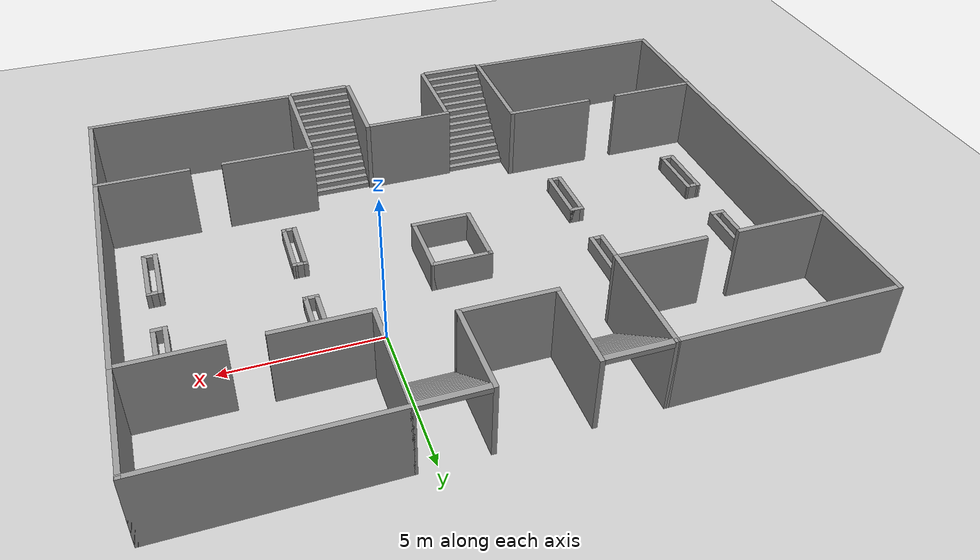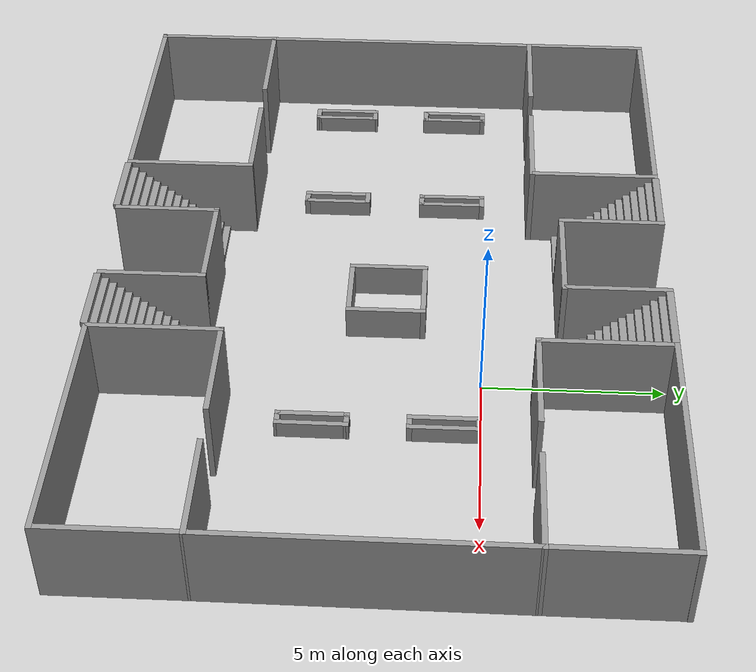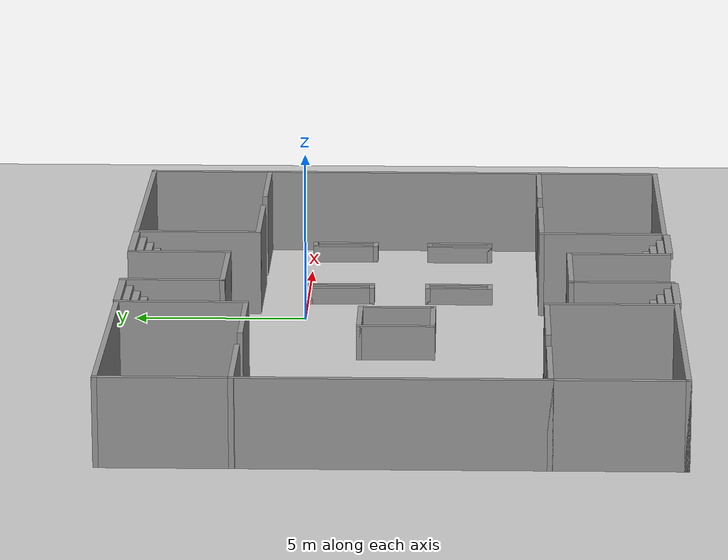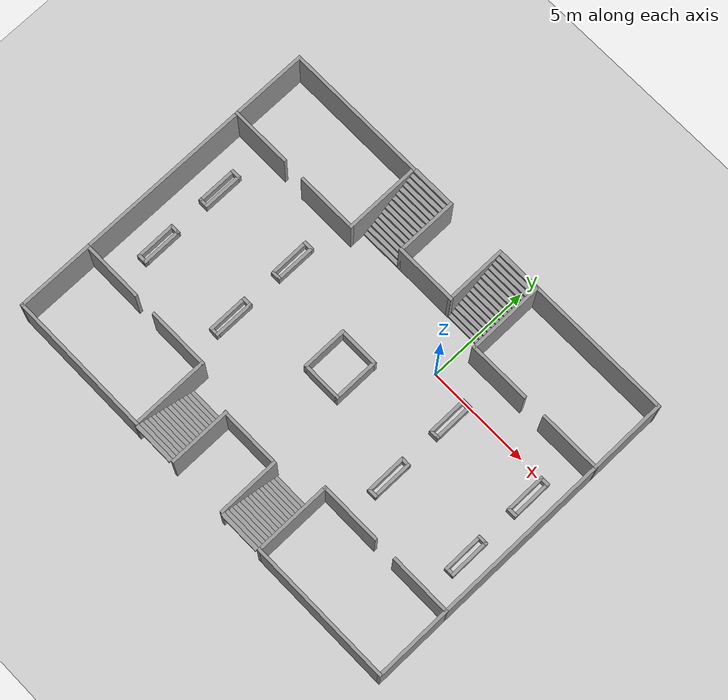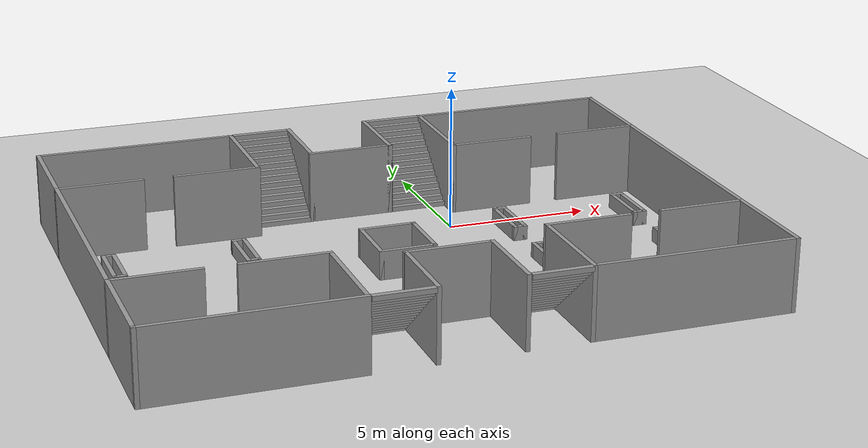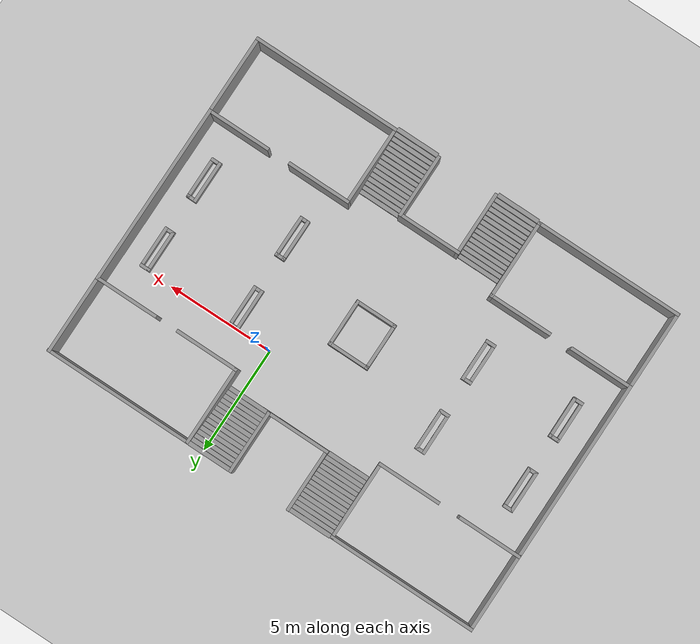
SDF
<sdf version="1.7">
 <world name="default">
  <light name="sun" type="directional">
   <pose>0 0 10 0 -0 0</pose>
   <diffuse>0.8 0.8 0.8 1</diffuse>
   <specular>0.2 0.2 0.2 1</specular>
   <attenuation>
    <range>1000</range>
    <constant>0.9</constant>
    <linear>0.01</linear>
    <quadratic>0.001</quadratic>
   </attenuation>
   <direction>-0.5 0.1 -0.9</direction>
   <spot><inner_angle>0</inner_angle><outer_angle>0</outer_angle><falloff>0</falloff></spot>
  </light>
  <model name="ground_plane">
   <static>1</static>
   <link name="link">
    <collision name="collision">
     <geometry><plane><normal>0 0 1</normal><size>100 100</size></plane></geometry>
     <surface>
      <contact><collide_bitmask>65535</collide_bitmask></contact>
      <friction><ode><mu>100</mu><mu2>50</mu2></ode></friction>
     </surface>
    </collision>
    <visual name="visual">
     <cast_shadows>0</cast_shadows>
     <geometry><plane><normal>0 0 1</normal><size>100 100</size></plane></geometry>
     <material>
      <script><uri>file://media/materials/scripts/gazebo.material</uri><name>Gazebo/Grey</name></script>
     </material>
    </visual>
   </link>
  </model>
  <gravity>0 0 -9.8</gravity>
  <magnetic_field>6e-06 2.3e-05 -4.2e-05</magnetic_field>
  <atmosphere type="adiabatic"/>
  <physics type="ode">
   <max_step_size>0.001</max_step_size>
   <real_time_factor>1</real_time_factor>
   <real_time_update_rate>1000</real_time_update_rate>
  </physics>
  <scene><ambient>0.4 0.4 0.4 1</ambient><background>0.7 0.7 0.7 1</background><shadows>1</shadows></scene>
  <audio><device>default</device></audio>
  <spherical_coordinates>
   <surface_model>EARTH_WGS84</surface_model>
   <latitude_deg>0</latitude_deg>
   <longitude_deg>0</longitude_deg>
   <elevation>0</elevation>
   <heading_deg>0</heading_deg>
  </spherical_coordinates>
  <model name="Lobby">
   <pose>-2.92426 -2.79933 0 0 -0 0</pose>
   <link name="Stairs_0">
    <visual name="Stairs_0_Visual_0">
     <pose>-2.50741 4.98625 0.083333 0 -0 -3.14159</pose>
     <geometry><box><size>2 0.2 0.166667</size></box></geometry>
     <material>
      <script><uri>file://media/materials/scripts/gazebo.material</uri><name>Gazebo/Grey</name></script>
      <ambient>1 1 1 1</ambient>
     </material>
     <meta><layer>0</layer></meta>
    </visual>
    <collision name="Stairs_0_Collision_0">
     <geometry><box><size>2 0.2 0.166667</size></box></geometry>
     <pose>-2.50741 4.98625 0.083333 0 -0 -3.14159</pose>
    </collision>
    <visual name="Stairs_0_Visual_1">
     <pose>-2.50741 5.18625 0.25 0 -0 -3.14159</pose>
     <geometry><box><size>2 0.2 0.166667</size></box></geometry>
     <material>
      <script><uri>file://media/materials/scripts/gazebo.material</uri><name>Gazebo/Grey</name></script>
      <ambient>1 1 1 1</ambient>
     </material>
     <meta><layer>0</layer></meta>
    </visual>
    <collision name="Stairs_0_Collision_1">
     <geometry><box><size>2 0.2 0.166667</size></box></geometry>
     <pose>-2.50741 5.18625 0.25 0 -0 -3.14159</pose>
    </collision>
    <visual name="Stairs_0_Visual_2">
     <pose>-2.50741 5.38624 0.416667 0 -0 -3.14159</pose>
     <geometry><box><size>2 0.2 0.166667</size></box></geometry>
     <material>
      <script><uri>file://media/materials/scripts/gazebo.material</uri><name>Gazebo/Grey</name></script>
      <ambient>1 1 1 1</ambient>
     </material>
     <meta><layer>0</layer></meta>
    </visual>
    <collision name="Stairs_0_Collision_2">
     <geometry><box><size>2 0.2 0.166667</size></box></geometry>
     <pose>-2.50741 5.38624 0.416667 0 -0 -3.14159</pose>
    </collision>
    <visual name="Stairs_0_Visual_3">
     <pose>-2.50741 5.58624 0.583333 0 -0 -3.14159</pose>
     <geometry><box><size>2 0.2 0.166667</size></box></geometry>
     <material>
      <script><uri>file://media/materials/scripts/gazebo.material</uri><name>Gazebo/Grey</name></script>
      <ambient>1 1 1 1</ambient>
     </material>
     <meta><layer>0</layer></meta>
    </visual>
    <collision name="Stairs_0_Collision_3">
     <geometry><box><size>2 0.2 0.166667</size></box></geometry>
     <pose>-2.50741 5.58624 0.583333 0 -0 -3.14159</pose>
    </collision>
    <visual name="Stairs_0_Visual_4">
     <pose>-2.50741 5.78625 0.75 0 -0 -3.14159</pose>
     <geometry><box><size>2 0.2 0.166667</size></box></geometry>
     <material>
      <script><uri>file://media/materials/scripts/gazebo.material</uri><name>Gazebo/Grey</name></script>
      <ambient>1 1 1 1</ambient>
     </material>
     <meta><layer>0</layer></meta>
    </visual>
    <collision name="Stairs_0_Collision_4">
     <geometry><box><size>2 0.2 0.166667</size></box></geometry>
     <pose>-2.50741 5.78625 0.75 0 -0 -3.14159</pose>
    </collision>
    <visual name="Stairs_0_Visual_5">
     <pose>-2.50741 5.98625 0.916667 0 -0 -3.14159</pose>
     <geometry><box><size>2 0.2 0.166667</size></box></geometry>
     <material>
      <script><uri>file://media/materials/scripts/gazebo.material</uri><name>Gazebo/Grey</name></script>
      <ambient>1 1 1 1</ambient>
     </material>
     <meta><layer>0</layer></meta>
    </visual>
    <collision name="Stairs_0_Collision_5">
     <geometry><box><size>2 0.2 0.166667</size></box></geometry>
     <pose>-2.50741 5.98625 0.916667 0 -0 -3.14159</pose>
    </collision>
    <visual name="Stairs_0_Visual_6">
     <pose>-2.50741 6.18625 1.08333 0 -0 -3.14159</pose>
     <geometry><box><size>2 0.2 0.166667</size></box></geometry>
     <material>
      <script><uri>file://media/materials/scripts/gazebo.material</uri><name>Gazebo/Grey</name></script>
      <ambient>1 1 1 1</ambient>
     </material>
     <meta><layer>0</layer></meta>
    </visual>
    <collision name="Stairs_0_Collision_6">
     <geometry><box><size>2 0.2 0.166667</size></box></geometry>
     <pose>-2.50741 6.18625 1.08333 0 -0 -3.14159</pose>
    </collision>
    <visual name="Stairs_0_Visual_7">
     <pose>-2.50741 6.38624 1.25 0 -0 -3.14159</pose>
     <geometry><box><size>2 0.2 0.166667</size></box></geometry>
     <material>
      <script><uri>file://media/materials/scripts/gazebo.material</uri><name>Gazebo/Grey</name></script>
      <ambient>1 1 1 1</ambient>
     </material>
     <meta><layer>0</layer></meta>
    </visual>
    <collision name="Stairs_0_Collision_7">
     <geometry><box><size>2 0.2 0.166667</size></box></geometry>
     <pose>-2.50741 6.38624 1.25 0 -0 -3.14159</pose>
    </collision>
    <visual name="Stairs_0_Visual_8">
     <pose>-2.50741 6.58625 1.41667 0 -0 -3.14159</pose>
     <geometry><box><size>2 0.2 0.166667</size></box></geometry>
     <material>
      <script><uri>file://media/materials/scripts/gazebo.material</uri><name>Gazebo/Grey</name></script>
      <ambient>1 1 1 1</ambient>
     </material>
     <meta><layer>0</layer></meta>
    </visual>
    <collision name="Stairs_0_Collision_8">
     <geometry><box><size>2 0.2 0.166667</size></box></geometry>
     <pose>-2.50741 6.58625 1.41667 0 -0 -3.14159</pose>
    </collision>
    <visual name="Stairs_0_Visual_9">
     <pose>-2.50741 6.78625 1.58333 0 -0 -3.14159</pose>
     <geometry><box><size>2 0.2 0.166667</size></box></geometry>
     <material>
      <script><uri>file://media/materials/scripts/gazebo.material</uri><name>Gazebo/Grey</name></script>
      <ambient>1 1 1 1</ambient>
     </material>
     <meta><layer>0</layer></meta>
    </visual>
    <collision name="Stairs_0_Collision_9">
     <geometry><box><size>2 0.2 0.166667</size></box></geometry>
     <pose>-2.50741 6.78625 1.58333 0 -0 -3.14159</pose>
    </collision>
    <visual name="Stairs_0_Visual_10">
     <pose>-2.50741 6.98625 1.75 0 -0 -3.14159</pose>
     <geometry><box><size>2 0.2 0.166667</size></box></geometry>
     <material>
      <script><uri>file://media/materials/scripts/gazebo.material</uri><name>Gazebo/Grey</name></script>
      <ambient>1 1 1 1</ambient>
     </material>
     <meta><layer>0</layer></meta>
    </visual>
    <collision name="Stairs_0_Collision_10">
     <geometry><box><size>2 0.2 0.166667</size></box></geometry>
     <pose>-2.50741 6.98625 1.75 0 -0 -3.14159</pose>
    </collision>
    <visual name="Stairs_0_Visual_11">
     <pose>-2.50741 7.18625 1.91667 0 -0 -3.14159</pose>
     <geometry><box><size>2 0.2 0.166667</size></box></geometry>
     <material>
      <script><uri>file://media/materials/scripts/gazebo.material</uri><name>Gazebo/Grey</name></script>
      <ambient>1 1 1 1</ambient>
     </material>
     <meta><layer>0</layer></meta>
    </visual>
    <collision name="Stairs_0_Collision_11">
     <geometry><box><size>2 0.2 0.166667</size></box></geometry>
     <pose>-2.50741 7.18625 1.91667 0 -0 -3.14159</pose>
    </collision>
    <visual name="Stairs_0_Visual_12">
     <pose>-2.50741 7.38624 2.08333 0 -0 -3.14159</pose>
     <geometry><box><size>2 0.2 0.166667</size></box></geometry>
     <material>
      <script><uri>file://media/materials/scripts/gazebo.material</uri><name>Gazebo/Grey</name></script>
      <ambient>1 1 1 1</ambient>
     </material>
     <meta><layer>0</layer></meta>
    </visual>
    <collision name="Stairs_0_Collision_12">
     <geometry><box><size>2 0.2 0.166667</size></box></geometry>
     <pose>-2.50741 7.38624 2.08333 0 -0 -3.14159</pose>
    </collision>
    <visual name="Stairs_0_Visual_13">
     <pose>-2.50741 7.58625 2.25 0 -0 -3.14159</pose>
     <geometry><box><size>2 0.2 0.166667</size></box></geometry>
     <material>
      <script><uri>file://media/materials/scripts/gazebo.material</uri><name>Gazebo/Grey</name></script>
      <ambient>1 1 1 1</ambient>
     </material>
     <meta><layer>0</layer></meta>
    </visual>
    <collision name="Stairs_0_Collision_13">
     <geometry><box><size>2 0.2 0.166667</size></box></geometry>
     <pose>-2.50741 7.58625 2.25 0 -0 -3.14159</pose>
    </collision>
    <visual name="Stairs_0_Visual_14">
     <pose>-2.50741 7.78625 2.41667 0 -0 -3.14159</pose>
     <geometry><box><size>2 0.2 0.166667</size></box></geometry>
     <material>
      <script><uri>file://media/materials/scripts/gazebo.material</uri><name>Gazebo/Grey</name></script>
      <ambient>1 1 1 1</ambient>
     </material>
     <meta><layer>0</layer></meta>
    </visual>
    <collision name="Stairs_0_Collision_14">
     <geometry><box><size>2 0.2 0.166667</size></box></geometry>
     <pose>-2.50741 7.78625 2.41667 0 -0 -3.14159</pose>
    </collision>
   </link>
   <link name="Stairs_1">
    <visual name="Stairs_1_Visual_0">
     <pose>2.48797 5.00037 0.083333 0 -0 -3.14159</pose>
     <geometry><box><size>2 0.2 0.166667</size></box></geometry>
     <material>
      <script><uri>file://media/materials/scripts/gazebo.material</uri><name>Gazebo/Grey</name></script>
      <ambient>1 1 1 1</ambient>
     </material>
     <meta><layer>0</layer></meta>
    </visual>
    <collision name="Stairs_1_Collision_0">
     <geometry><box><size>2 0.2 0.166667</size></box></geometry>
     <pose>2.48797 5.00037 0.083333 0 -0 -3.14159</pose>
    </collision>
    <visual name="Stairs_1_Visual_1">
     <pose>2.48797 5.20037 0.25 0 -0 -3.14159</pose>
     <geometry><box><size>2 0.2 0.166667</size></box></geometry>
     <material>
      <script><uri>file://media/materials/scripts/gazebo.material</uri><name>Gazebo/Grey</name></script>
      <ambient>1 1 1 1</ambient>
     </material>
     <meta><layer>0</layer></meta>
    </visual>
    <collision name="Stairs_1_Collision_1">
     <geometry><box><size>2 0.2 0.166667</size></box></geometry>
     <pose>2.48797 5.20037 0.25 0 -0 -3.14159</pose>
    </collision>
    <visual name="Stairs_1_Visual_2">
     <pose>2.48797 5.40037 0.416667 0 -0 -3.14159</pose>
     <geometry><box><size>2 0.2 0.166667</size></box></geometry>
     <material>
      <script><uri>file://media/materials/scripts/gazebo.material</uri><name>Gazebo/Grey</name></script>
      <ambient>1 1 1 1</ambient>
     </material>
     <meta><layer>0</layer></meta>
    </visual>
    <collision name="Stairs_1_Collision_2">
     <geometry><box><size>2 0.2 0.166667</size></box></geometry>
     <pose>2.48797 5.40037 0.416667 0 -0 -3.14159</pose>
    </collision>
    <visual name="Stairs_1_Visual_3">
     <pose>2.48797 5.60037 0.583333 0 -0 -3.14159</pose>
     <geometry><box><size>2 0.2 0.166667</size></box></geometry>
     <material>
      <script><uri>file://media/materials/scripts/gazebo.material</uri><name>Gazebo/Grey</name></script>
      <ambient>1 1 1 1</ambient>
     </material>
     <meta><layer>0</layer></meta>
    </visual>
    <collision name="Stairs_1_Collision_3">
     <geometry><box><size>2 0.2 0.166667</size></box></geometry>
     <pose>2.48797 5.60037 0.583333 0 -0 -3.14159</pose>
    </collision>
    <visual name="Stairs_1_Visual_4">
     <pose>2.48797 5.80037 0.75 0 -0 -3.14159</pose>
     <geometry><box><size>2 0.2 0.166667</size></box></geometry>
     <material>
      <script><uri>file://media/materials/scripts/gazebo.material</uri><name>Gazebo/Grey</name></script>
      <ambient>1 1 1 1</ambient>
     </material>
     <meta><layer>0</layer></meta>
    </visual>
    <collision name="Stairs_1_Collision_4">
     <geometry><box><size>2 0.2 0.166667</size></box></geometry>
     <pose>2.48797 5.80037 0.75 0 -0 -3.14159</pose>
    </collision>
    <visual name="Stairs_1_Visual_5">
     <pose>2.48797 6.00037 0.916667 0 -0 -3.14159</pose>
     <geometry><box><size>2 0.2 0.166667</size></box></geometry>
     <material>
      <script><uri>file://media/materials/scripts/gazebo.material</uri><name>Gazebo/Grey</name></script>
      <ambient>1 1 1 1</ambient>
     </material>
     <meta><layer>0</layer></meta>
    </visual>
    <collision name="Stairs_1_Collision_5">
     <geometry><box><size>2 0.2 0.166667</size></box></geometry>
     <pose>2.48797 6.00037 0.916667 0 -0 -3.14159</pose>
    </collision>
    <visual name="Stairs_1_Visual_6">
     <pose>2.48797 6.20037 1.08333 0 -0 -3.14159</pose>
     <geometry><box><size>2 0.2 0.166667</size></box></geometry>
     <material>
      <script><uri>file://media/materials/scripts/gazebo.material</uri><name>Gazebo/Grey</name></script>
      <ambient>1 1 1 1</ambient>
     </material>
     <meta><layer>0</layer></meta>
    </visual>
    <collision name="Stairs_1_Collision_6">
     <geometry><box><size>2 0.2 0.166667</size></box></geometry>
     <pose>2.48797 6.20037 1.08333 0 -0 -3.14159</pose>
    </collision>
    <visual name="Stairs_1_Visual_7">
     <pose>2.48797 6.40037 1.25 0 -0 -3.14159</pose>
     <geometry><box><size>2 0.2 0.166667</size></box></geometry>
     <material>
      <script><uri>file://media/materials/scripts/gazebo.material</uri><name>Gazebo/Grey</name></script>
      <ambient>1 1 1 1</ambient>
     </material>
     <meta><layer>0</layer></meta>
    </visual>
    <collision name="Stairs_1_Collision_7">
     <geometry><box><size>2 0.2 0.166667</size></box></geometry>
     <pose>2.48797 6.40037 1.25 0 -0 -3.14159</pose>
    </collision>
    <visual name="Stairs_1_Visual_8">
     <pose>2.48797 6.60037 1.41667 0 -0 -3.14159</pose>
     <geometry><box><size>2 0.2 0.166667</size></box></geometry>
     <material>
      <script><uri>file://media/materials/scripts/gazebo.material</uri><name>Gazebo/Grey</name></script>
      <ambient>1 1 1 1</ambient>
     </material>
     <meta><layer>0</layer></meta>
    </visual>
    <collision name="Stairs_1_Collision_8">
     <geometry><box><size>2 0.2 0.166667</size></box></geometry>
     <pose>2.48797 6.60037 1.41667 0 -0 -3.14159</pose>
    </collision>
    <visual name="Stairs_1_Visual_9">
     <pose>2.48797 6.80037 1.58333 0 -0 -3.14159</pose>
     <geometry><box><size>2 0.2 0.166667</size></box></geometry>
     <material>
      <script><uri>file://media/materials/scripts/gazebo.material</uri><name>Gazebo/Grey</name></script>
      <ambient>1 1 1 1</ambient>
     </material>
     <meta><layer>0</layer></meta>
    </visual>
    <collision name="Stairs_1_Collision_9">
     <geometry><box><size>2 0.2 0.166667</size></box></geometry>
     <pose>2.48797 6.80037 1.58333 0 -0 -3.14159</pose>
    </collision>
    <visual name="Stairs_1_Visual_10">
     <pose>2.48797 7.00037 1.75 0 -0 -3.14159</pose>
     <geometry><box><size>2 0.2 0.166667</size></box></geometry>
     <material>
      <script><uri>file://media/materials/scripts/gazebo.material</uri><name>Gazebo/Grey</name></script>
      <ambient>1 1 1 1</ambient>
     </material>
     <meta><layer>0</layer></meta>
    </visual>
    <collision name="Stairs_1_Collision_10">
     <geometry><box><size>2 0.2 0.166667</size></box></geometry>
     <pose>2.48797 7.00037 1.75 0 -0 -3.14159</pose>
    </collision>
    <visual name="Stairs_1_Visual_11">
     <pose>2.48797 7.20037 1.91667 0 -0 -3.14159</pose>
     <geometry><box><size>2 0.2 0.166667</size></box></geometry>
     <material>
      <script><uri>file://media/materials/scripts/gazebo.material</uri><name>Gazebo/Grey</name></script>
      <ambient>1 1 1 1</ambient>
     </material>
     <meta><layer>0</layer></meta>
    </visual>
    <collision name="Stairs_1_Collision_11">
     <geometry><box><size>2 0.2 0.166667</size></box></geometry>
     <pose>2.48797 7.20037 1.91667 0 -0 -3.14159</pose>
    </collision>
    <visual name="Stairs_1_Visual_12">
     <pose>2.48797 7.40037 2.08333 0 -0 -3.14159</pose>
     <geometry><box><size>2 0.2 0.166667</size></box></geometry>
     <material>
      <script><uri>file://media/materials/scripts/gazebo.material</uri><name>Gazebo/Grey</name></script>
      <ambient>1 1 1 1</ambient>
     </material>
     <meta><layer>0</layer></meta>
    </visual>
    <collision name="Stairs_1_Collision_12">
     <geometry><box><size>2 0.2 0.166667</size></box></geometry>
     <pose>2.48797 7.40037 2.08333 0 -0 -3.14159</pose>
    </collision>
    <visual name="Stairs_1_Visual_13">
     <pose>2.48797 7.60037 2.25 0 -0 -3.14159</pose>
     <geometry><box><size>2 0.2 0.166667</size></box></geometry>
     <material>
      <script><uri>file://media/materials/scripts/gazebo.material</uri><name>Gazebo/Grey</name></script>
      <ambient>1 1 1 1</ambient>
     </material>
     <meta><layer>0</layer></meta>
    </visual>
    <collision name="Stairs_1_Collision_13">
     <geometry><box><size>2 0.2 0.166667</size></box></geometry>
     <pose>2.48797 7.60037 2.25 0 -0 -3.14159</pose>
    </collision>
    <visual name="Stairs_1_Visual_14">
     <pose>2.48797 7.80037 2.41667 0 -0 -3.14159</pose>
     <geometry><box><size>2 0.2 0.166667</size></box></geometry>
     <material>
      <script><uri>file://media/materials/scripts/gazebo.material</uri><name>Gazebo/Grey</name></script>
      <ambient>1 1 1 1</ambient>
     </material>
     <meta><layer>0</layer></meta>
    </visual>
    <collision name="Stairs_1_Collision_14">
     <geometry><box><size>2 0.2 0.166667</size></box></geometry>
     <pose>2.48797 7.80037 2.41667 0 -0 -3.14159</pose>
    </collision>
   </link>
   <link name="Stairs_2">
    <visual name="Stairs_2_Visual_0">
     <pose>-2.50769 -5.00037 0.083333 0 -0 0</pose>
     <geometry><box><size>2 0.2 0.166667</size></box></geometry>
     <material>
      <script><uri>file://media/materials/scripts/gazebo.material</uri><name>Gazebo/Grey</name></script>
      <ambient>1 1 1 1</ambient>
     </material>
     <meta><layer>0</layer></meta>
    </visual>
    <collision name="Stairs_2_Collision_0">
     <geometry><box><size>2 0.2 0.166667</size></box></geometry>
     <pose>-2.50769 -5.00037 0.083333 0 -0 0</pose>
    </collision>
    <visual name="Stairs_2_Visual_1">
     <pose>-2.50769 -5.20037 0.25 0 -0 0</pose>
     <geometry><box><size>2 0.2 0.166667</size></box></geometry>
     <material>
      <script><uri>file://media/materials/scripts/gazebo.material</uri><name>Gazebo/Grey</name></script>
      <ambient>1 1 1 1</ambient>
     </material>
     <meta><layer>0</layer></meta>
    </visual>
    <collision name="Stairs_2_Collision_1">
     <geometry><box><size>2 0.2 0.166667</size></box></geometry>
     <pose>-2.50769 -5.20037 0.25 0 -0 0</pose>
    </collision>
    <visual name="Stairs_2_Visual_2">
     <pose>-2.50769 -5.40037 0.416667 0 -0 0</pose>
     <geometry><box><size>2 0.2 0.166667</size></box></geometry>
     <material>
      <script><uri>file://media/materials/scripts/gazebo.material</uri><name>Gazebo/Grey</name></script>
      <ambient>1 1 1 1</ambient>
     </material>
     <meta><layer>0</layer></meta>
    </visual>
    <collision name="Stairs_2_Collision_2">
     <geometry><box><size>2 0.2 0.166667</size></box></geometry>
     <pose>-2.50769 -5.40037 0.416667 0 -0 0</pose>
    </collision>
    <visual name="Stairs_2_Visual_3">
     <pose>-2.50769 -5.60037 0.583333 0 -0 0</pose>
     <geometry><box><size>2 0.2 0.166667</size></box></geometry>
     <material>
      <script><uri>file://media/materials/scripts/gazebo.material</uri><name>Gazebo/Grey</name></script>
      <ambient>1 1 1 1</ambient>
     </material>
     <meta><layer>0</layer></meta>
    </visual>
    <collision name="Stairs_2_Collision_3">
     <geometry><box><size>2 0.2 0.166667</size></box></geometry>
     <pose>-2.50769 -5.60037 0.583333 0 -0 0</pose>
    </collision>
    <visual name="Stairs_2_Visual_4">
     <pose>-2.50769 -5.80037 0.75 0 -0 0</pose>
     <geometry><box><size>2 0.2 0.166667</size></box></geometry>
     <material>
      <script><uri>file://media/materials/scripts/gazebo.material</uri><name>Gazebo/Grey</name></script>
      <ambient>1 1 1 1</ambient>
     </material>
     <meta><layer>0</layer></meta>
    </visual>
    <collision name="Stairs_2_Collision_4">
     <geometry><box><size>2 0.2 0.166667</size></box></geometry>
     <pose>-2.50769 -5.80037 0.75 0 -0 0</pose>
    </collision>
    <visual name="Stairs_2_Visual_5">
     <pose>-2.50769 -6.00037 0.916667 0 -0 0</pose>
     <geometry><box><size>2 0.2 0.166667</size></box></geometry>
     <material>
      <script><uri>file://media/materials/scripts/gazebo.material</uri><name>Gazebo/Grey</name></script>
      <ambient>1 1 1 1</ambient>
     </material>
     <meta><layer>0</layer></meta>
    </visual>
    <collision name="Stairs_2_Collision_5">
     <geometry><box><size>2 0.2 0.166667</size></box></geometry>
     <pose>-2.50769 -6.00037 0.916667 0 -0 0</pose>
    </collision>
    <visual name="Stairs_2_Visual_6">
     <pose>-2.50769 -6.20037 1.08333 0 -0 0</pose>
     <geometry><box><size>2 0.2 0.166667</size></box></geometry>
     <material>
      <script><uri>file://media/materials/scripts/gazebo.material</uri><name>Gazebo/Grey</name></script>
      <ambient>1 1 1 1</ambient>
     </material>
     <meta><layer>0</layer></meta>
    </visual>
    <collision name="Stairs_2_Collision_6">
     <geometry><box><size>2 0.2 0.166667</size></box></geometry>
     <pose>-2.50769 -6.20037 1.08333 0 -0 0</pose>
    </collision>
    <visual name="Stairs_2_Visual_7">
     <pose>-2.50769 -6.40037 1.25 0 -0 0</pose>
     <geometry><box><size>2 0.2 0.166667</size></box></geometry>
     <material>
      <script><uri>file://media/materials/scripts/gazebo.material</uri><name>Gazebo/Grey</name></script>
      <ambient>1 1 1 1</ambient>
     </material>
     <meta><layer>0</layer></meta>
    </visual>
    <collision name="Stairs_2_Collision_7">
     <geometry><box><size>2 0.2 0.166667</size></box></geometry>
     <pose>-2.50769 -6.40037 1.25 0 -0 0</pose>
    </collision>
    <visual name="Stairs_2_Visual_8">
     <pose>-2.50769 -6.60037 1.41667 0 -0 0</pose>
     <geometry><box><size>2 0.2 0.166667</size></box></geometry>
     <material>
      <script><uri>file://media/materials/scripts/gazebo.material</uri><name>Gazebo/Grey</name></script>
      <ambient>1 1 1 1</ambient>
     </material>
     <meta><layer>0</layer></meta>
    </visual>
    <collision name="Stairs_2_Collision_8">
     <geometry><box><size>2 0.2 0.166667</size></box></geometry>
     <pose>-2.50769 -6.60037 1.41667 0 -0 0</pose>
    </collision>
    <visual name="Stairs_2_Visual_9">
     <pose>-2.50769 -6.80037 1.58333 0 -0 0</pose>
     <geometry><box><size>2 0.2 0.166667</size></box></geometry>
     <material>
      <script><uri>file://media/materials/scripts/gazebo.material</uri><name>Gazebo/Grey</name></script>
      <ambient>1 1 1 1</ambient>
     </material>
     <meta><layer>0</layer></meta>
    </visual>
    <collision name="Stairs_2_Collision_9">
     <geometry><box><size>2 0.2 0.166667</size></box></geometry>
     <pose>-2.50769 -6.80037 1.58333 0 -0 0</pose>
    </collision>
    <visual name="Stairs_2_Visual_10">
     <pose>-2.50769 -7.00037 1.75 0 -0 0</pose>
     <geometry><box><size>2 0.2 0.166667</size></box></geometry>
     <material>
      <script><uri>file://media/materials/scripts/gazebo.material</uri><name>Gazebo/Grey</name></script>
      <ambient>1 1 1 1</ambient>
     </material>
     <meta><layer>0</layer></meta>
    </visual>
    <collision name="Stairs_2_Collision_10">
     <geometry><box><size>2 0.2 0.166667</size></box></geometry>
     <pose>-2.50769 -7.00037 1.75 0 -0 0</pose>
    </collision>
    <visual name="Stairs_2_Visual_11">
     <pose>-2.50769 -7.20037 1.91667 0 -0 0</pose>
     <geometry><box><size>2 0.2 0.166667</size></box></geometry>
     <material>
      <script><uri>file://media/materials/scripts/gazebo.material</uri><name>Gazebo/Grey</name></script>
      <ambient>1 1 1 1</ambient>
     </material>
     <meta><layer>0</layer></meta>
    </visual>
    <collision name="Stairs_2_Collision_11">
     <geometry><box><size>2 0.2 0.166667</size></box></geometry>
     <pose>-2.50769 -7.20037 1.91667 0 -0 0</pose>
    </collision>
    <visual name="Stairs_2_Visual_12">
     <pose>-2.50769 -7.40037 2.08333 0 -0 0</pose>
     <geometry><box><size>2 0.2 0.166667</size></box></geometry>
     <material>
      <script><uri>file://media/materials/scripts/gazebo.material</uri><name>Gazebo/Grey</name></script>
      <ambient>1 1 1 1</ambient>
     </material>
     <meta><layer>0</layer></meta>
    </visual>
    <collision name="Stairs_2_Collision_12">
     <geometry><box><size>2 0.2 0.166667</size></box></geometry>
     <pose>-2.50769 -7.40037 2.08333 0 -0 0</pose>
    </collision>
    <visual name="Stairs_2_Visual_13">
     <pose>-2.50769 -7.60037 2.25 0 -0 0</pose>
     <geometry><box><size>2 0.2 0.166667</size></box></geometry>
     <material>
      <script><uri>file://media/materials/scripts/gazebo.material</uri><name>Gazebo/Grey</name></script>
      <ambient>1 1 1 1</ambient>
     </material>
     <meta><layer>0</layer></meta>
    </visual>
    <collision name="Stairs_2_Collision_13">
     <geometry><box><size>2 0.2 0.166667</size></box></geometry>
     <pose>-2.50769 -7.60037 2.25 0 -0 0</pose>
    </collision>
    <visual name="Stairs_2_Visual_14">
     <pose>-2.50769 -7.80037 2.41667 0 -0 0</pose>
     <geometry><box><size>2 0.2 0.166667</size></box></geometry>
     <material>
      <script><uri>file://media/materials/scripts/gazebo.material</uri><name>Gazebo/Grey</name></script>
      <ambient>1 1 1 1</ambient>
     </material>
     <meta><layer>0</layer></meta>
    </visual>
    <collision name="Stairs_2_Collision_14">
     <geometry><box><size>2 0.2 0.166667</size></box></geometry>
     <pose>-2.50769 -7.80037 2.41667 0 -0 0</pose>
    </collision>
   </link>
   <link name="Stairs_3">
    <visual name="Stairs_3_Visual_0">
     <pose>2.48331 -4.98887 0.083333 0 -0 0</pose>
     <geometry><box><size>2 0.2 0.166667</size></box></geometry>
     <material>
      <script><uri>file://media/materials/scripts/gazebo.material</uri><name>Gazebo/Grey</name></script>
      <ambient>1 1 1 1</ambient>
     </material>
     <meta><layer>0</layer></meta>
    </visual>
    <collision name="Stairs_3_Collision_0">
     <geometry><box><size>2 0.2 0.166667</size></box></geometry>
     <pose>2.48331 -4.98887 0.083333 0 -0 0</pose>
    </collision>
    <visual name="Stairs_3_Visual_1">
     <pose>2.48331 -5.18887 0.25 0 -0 0</pose>
     <geometry><box><size>2 0.2 0.166667</size></box></geometry>
     <material>
      <script><uri>file://media/materials/scripts/gazebo.material</uri><name>Gazebo/Grey</name></script>
      <ambient>1 1 1 1</ambient>
     </material>
     <meta><layer>0</layer></meta>
    </visual>
    <collision name="Stairs_3_Collision_1">
     <geometry><box><size>2 0.2 0.166667</size></box></geometry>
     <pose>2.48331 -5.18887 0.25 0 -0 0</pose>
    </collision>
    <visual name="Stairs_3_Visual_2">
     <pose>2.48331 -5.38887 0.416667 0 -0 0</pose>
     <geometry><box><size>2 0.2 0.166667</size></box></geometry>
     <material>
      <script><uri>file://media/materials/scripts/gazebo.material</uri><name>Gazebo/Grey</name></script>
      <ambient>1 1 1 1</ambient>
     </material>
     <meta><layer>0</layer></meta>
    </visual>
    <collision name="Stairs_3_Collision_2">
     <geometry><box><size>2 0.2 0.166667</size></box></geometry>
     <pose>2.48331 -5.38887 0.416667 0 -0 0</pose>
    </collision>
    <visual name="Stairs_3_Visual_3">
     <pose>2.48331 -5.58887 0.583333 0 -0 0</pose>
     <geometry><box><size>2 0.2 0.166667</size></box></geometry>
     <material>
      <script><uri>file://media/materials/scripts/gazebo.material</uri><name>Gazebo/Grey</name></script>
      <ambient>1 1 1 1</ambient>
     </material>
     <meta><layer>0</layer></meta>
    </visual>
    <collision name="Stairs_3_Collision_3">
     <geometry><box><size>2 0.2 0.166667</size></box></geometry>
     <pose>2.48331 -5.58887 0.583333 0 -0 0</pose>
    </collision>
    <visual name="Stairs_3_Visual_4">
     <pose>2.48331 -5.78887 0.75 0 -0 0</pose>
     <geometry><box><size>2 0.2 0.166667</size></box></geometry>
     <material>
      <script><uri>file://media/materials/scripts/gazebo.material</uri><name>Gazebo/Grey</name></script>
      <ambient>1 1 1 1</ambient>
     </material>
     <meta><layer>0</layer></meta>
    </visual>
    <collision name="Stairs_3_Collision_4">
     <geometry><box><size>2 0.2 0.166667</size></box></geometry>
     <pose>2.48331 -5.78887 0.75 0 -0 0</pose>
    </collision>
    <visual name="Stairs_3_Visual_5">
     <pose>2.48331 -5.98887 0.916667 0 -0 0</pose>
     <geometry><box><size>2 0.2 0.166667</size></box></geometry>
     <material>
      <script><uri>file://media/materials/scripts/gazebo.material</uri><name>Gazebo/Grey</name></script>
      <ambient>1 1 1 1</ambient>
     </material>
     <meta><layer>0</layer></meta>
    </visual>
    <collision name="Stairs_3_Collision_5">
     <geometry><box><size>2 0.2 0.166667</size></box></geometry>
     <pose>2.48331 -5.98887 0.916667 0 -0 0</pose>
    </collision>
    <visual name="Stairs_3_Visual_6">
     <pose>2.48331 -6.18887 1.08333 0 -0 0</pose>
     <geometry><box><size>2 0.2 0.166667</size></box></geometry>
     <material>
      <script><uri>file://media/materials/scripts/gazebo.material</uri><name>Gazebo/Grey</name></script>
      <ambient>1 1 1 1</ambient>
     </material>
     <meta><layer>0</layer></meta>
    </visual>
    <collision name="Stairs_3_Collision_6">
     <geometry><box><size>2 0.2 0.166667</size></box></geometry>
     <pose>2.48331 -6.18887 1.08333 0 -0 0</pose>
    </collision>
    <visual name="Stairs_3_Visual_7">
     <pose>2.48331 -6.38887 1.25 0 -0 0</pose>
     <geometry><box><size>2 0.2 0.166667</size></box></geometry>
     <material>
      <script><uri>file://media/materials/scripts/gazebo.material</uri><name>Gazebo/Grey</name></script>
      <ambient>1 1 1 1</ambient>
     </material>
     <meta><layer>0</layer></meta>
    </visual>
    <collision name="Stairs_3_Collision_7">
     <geometry><box><size>2 0.2 0.166667</size></box></geometry>
     <pose>2.48331 -6.38887 1.25 0 -0 0</pose>
    </collision>
    <visual name="Stairs_3_Visual_8">
     <pose>2.48331 -6.58887 1.41667 0 -0 0</pose>
     <geometry><box><size>2 0.2 0.166667</size></box></geometry>
     <material>
      <script><uri>file://media/materials/scripts/gazebo.material</uri><name>Gazebo/Grey</name></script>
      <ambient>1 1 1 1</ambient>
     </material>
     <meta><layer>0</layer></meta>
    </visual>
    <collision name="Stairs_3_Collision_8">
     <geometry><box><size>2 0.2 0.166667</size></box></geometry>
     <pose>2.48331 -6.58887 1.41667 0 -0 0</pose>
    </collision>
    <visual name="Stairs_3_Visual_9">
     <pose>2.48331 -6.78887 1.58333 0 -0 0</pose>
     <geometry><box><size>2 0.2 0.166667</size></box></geometry>
     <material>
      <script><uri>file://media/materials/scripts/gazebo.material</uri><name>Gazebo/Grey</name></script>
      <ambient>1 1 1 1</ambient>
     </material>
     <meta><layer>0</layer></meta>
    </visual>
    <collision name="Stairs_3_Collision_9">
     <geometry><box><size>2 0.2 0.166667</size></box></geometry>
     <pose>2.48331 -6.78887 1.58333 0 -0 0</pose>
    </collision>
    <visual name="Stairs_3_Visual_10">
     <pose>2.48331 -6.98887 1.75 0 -0 0</pose>
     <geometry><box><size>2 0.2 0.166667</size></box></geometry>
     <material>
      <script><uri>file://media/materials/scripts/gazebo.material</uri><name>Gazebo/Grey</name></script>
      <ambient>1 1 1 1</ambient>
     </material>
     <meta><layer>0</layer></meta>
    </visual>
    <collision name="Stairs_3_Collision_10">
     <geometry><box><size>2 0.2 0.166667</size></box></geometry>
     <pose>2.48331 -6.98887 1.75 0 -0 0</pose>
    </collision>
    <visual name="Stairs_3_Visual_11">
     <pose>2.48331 -7.18887 1.91667 0 -0 0</pose>
     <geometry><box><size>2 0.2 0.166667</size></box></geometry>
     <material>
      <script><uri>file://media/materials/scripts/gazebo.material</uri><name>Gazebo/Grey</name></script>
      <ambient>1 1 1 1</ambient>
     </material>
     <meta><layer>0</layer></meta>
    </visual>
    <collision name="Stairs_3_Collision_11">
     <geometry><box><size>2 0.2 0.166667</size></box></geometry>
     <pose>2.48331 -7.18887 1.91667 0 -0 0</pose>
    </collision>
    <visual name="Stairs_3_Visual_12">
     <pose>2.48331 -7.38887 2.08333 0 -0 0</pose>
     <geometry><box><size>2 0.2 0.166667</size></box></geometry>
     <material>
      <script><uri>file://media/materials/scripts/gazebo.material</uri><name>Gazebo/Grey</name></script>
      <ambient>1 1 1 1</ambient>
     </material>
     <meta><layer>0</layer></meta>
    </visual>
    <collision name="Stairs_3_Collision_12">
     <geometry><box><size>2 0.2 0.166667</size></box></geometry>
     <pose>2.48331 -7.38887 2.08333 0 -0 0</pose>
    </collision>
    <visual name="Stairs_3_Visual_13">
     <pose>2.48331 -7.58887 2.25 0 -0 0</pose>
     <geometry><box><size>2 0.2 0.166667</size></box></geometry>
     <material>
      <script><uri>file://media/materials/scripts/gazebo.material</uri><name>Gazebo/Grey</name></script>
      <ambient>1 1 1 1</ambient>
     </material>
     <meta><layer>0</layer></meta>
    </visual>
    <collision name="Stairs_3_Collision_13">
     <geometry><box><size>2 0.2 0.166667</size></box></geometry>
     <pose>2.48331 -7.58887 2.25 0 -0 0</pose>
    </collision>
    <visual name="Stairs_3_Visual_14">
     <pose>2.48331 -7.78887 2.41667 0 -0 0</pose>
     <geometry><box><size>2 0.2 0.166667</size></box></geometry>
     <material>
      <script><uri>file://media/materials/scripts/gazebo.material</uri><name>Gazebo/Grey</name></script>
      <ambient>1 1 1 1</ambient>
     </material>
     <meta><layer>0</layer></meta>
    </visual>
    <collision name="Stairs_3_Collision_14">
     <geometry><box><size>2 0.2 0.166667</size></box></geometry>
     <pose>2.48331 -7.78887 2.41667 0 -0 0</pose>
    </collision>
   </link>
   <link name="Wall_108">
    <collision name="Wall_108_Collision">
     <geometry><box><size>2 0.15 0.5</size></box></geometry>
     <pose>0 0 0.25 0 -0 0</pose>
    </collision>
    <visual name="Wall_108_Visual">
     <pose>0 0 0.25 0 -0 0</pose>
     <geometry><box><size>2 0.15 0.5</size></box></geometry>
     <material>
      <script><uri>file://media/materials/scripts/gazebo.material</uri><name>Gazebo/Grey</name></script>
      <ambient>1 1 1 1</ambient>
     </material>
     <meta><layer>0</layer></meta>
    </visual>
    <pose>9.42426 1.82533 0 0 -0 -1.5708</pose>
   </link>
   <link name="Wall_109">
    <collision name="Wall_109_Collision">
     <geometry><box><size>0.5 0.15 0.5</size></box></geometry>
     <pose>0 0 0.25 0 -0 0</pose>
    </collision>
    <visual name="Wall_109_Visual">
     <pose>0 0 0.25 0 -0 0</pose>
     <geometry><box><size>0.5 0.15 0.5</size></box></geometry>
     <material>
      <script><uri>file://media/materials/scripts/gazebo.material</uri><name>Gazebo/Grey</name></script>
      <ambient>1 1 1 1</ambient>
     </material>
     <meta><layer>0</layer></meta>
    </visual>
    <pose>9.24926 0.900328 0 0 -0 3.14159</pose>
   </link>
   <link name="Wall_110">
    <collision name="Wall_110_Collision">
     <geometry><box><size>2 0.15 0.5</size></box></geometry>
     <pose>0 0 0.25 0 -0 0</pose>
    </collision>
    <visual name="Wall_110_Visual">
     <pose>0 0 0.25 0 -0 0</pose>
     <geometry><box><size>2 0.15 0.5</size></box></geometry>
     <material>
      <script><uri>file://media/materials/scripts/gazebo.material</uri><name>Gazebo/Grey</name></script>
      <ambient>1 1 1 1</ambient>
     </material>
     <meta><layer>0</layer></meta>
    </visual>
    <pose>9.07426 1.82533 0 0 -0 1.5708</pose>
   </link>
   <link name="Wall_111">
    <collision name="Wall_111_Collision">
     <geometry><box><size>0.5 0.15 0.5</size></box></geometry>
     <pose>0 0 0.25 0 -0 0</pose>
    </collision>
    <visual name="Wall_111_Visual">
     <pose>0 0 0.25 0 -0 0</pose>
     <geometry><box><size>0.5 0.15 0.5</size></box></geometry>
     <material>
      <script><uri>file://media/materials/scripts/gazebo.material</uri><name>Gazebo/Grey</name></script>
      <ambient>1 1 1 1</ambient>
     </material>
     <meta><layer>0</layer></meta>
    </visual>
    <pose>9.24926 2.75033 0 0 -0 0</pose>
   </link>
   <link name="Wall_116">
    <collision name="Wall_116_Collision">
     <geometry><box><size>2 0.15 0.5</size></box></geometry>
     <pose>0 0 0.25 0 -0 0</pose>
    </collision>
    <visual name="Wall_116_Visual">
     <pose>0 0 0.25 0 -0 0</pose>
     <geometry><box><size>2 0.15 0.5</size></box></geometry>
     <material>
      <script><uri>file://media/materials/scripts/gazebo.material</uri><name>Gazebo/Grey</name></script>
      <ambient>1 1 1 1</ambient>
     </material>
     <meta><layer>0</layer></meta>
    </visual>
    <pose>9.39826 -1.69667 0 0 -0 -1.5708</pose>
   </link>
   <link name="Wall_117">
    <collision name="Wall_117_Collision">
     <geometry><box><size>0.5 0.15 0.5</size></box></geometry>
     <pose>0 0 0.25 0 -0 0</pose>
    </collision>
    <visual name="Wall_117_Visual">
     <pose>0 0 0.25 0 -0 0</pose>
     <geometry><box><size>0.5 0.15 0.5</size></box></geometry>
     <material>
      <script><uri>file://media/materials/scripts/gazebo.material</uri><name>Gazebo/Grey</name></script>
      <ambient>1 1 1 1</ambient>
     </material>
     <meta><layer>0</layer></meta>
    </visual>
    <pose>9.22326 -2.62167 0 0 -0 3.14159</pose>
   </link>
   <link name="Wall_118">
    <collision name="Wall_118_Collision">
     <geometry><box><size>2 0.15 0.5</size></box></geometry>
     <pose>0 0 0.25 0 -0 0</pose>
    </collision>
    <visual name="Wall_118_Visual">
     <pose>0 0 0.25 0 -0 0</pose>
     <geometry><box><size>2 0.15 0.5</size></box></geometry>
     <material>
      <script><uri>file://media/materials/scripts/gazebo.material</uri><name>Gazebo/Grey</name></script>
      <ambient>1 1 1 1</ambient>
     </material>
     <meta><layer>0</layer></meta>
    </visual>
    <pose>9.04826 -1.69667 0 0 -0 1.5708</pose>
   </link>
   <link name="Wall_119">
    <collision name="Wall_119_Collision">
     <geometry><box><size>0.5 0.15 0.5</size></box></geometry>
     <pose>0 0 0.25 0 -0 0</pose>
    </collision>
    <visual name="Wall_119_Visual">
     <pose>0 0 0.25 0 -0 0</pose>
     <geometry><box><size>0.5 0.15 0.5</size></box></geometry>
     <material>
      <script><uri>file://media/materials/scripts/gazebo.material</uri><name>Gazebo/Grey</name></script>
      <ambient>1 1 1 1</ambient>
     </material>
     <meta><layer>0</layer></meta>
    </visual>
    <pose>9.22326 -0.771672 0 0 -0 0</pose>
   </link>
   <link name="Wall_12">
    <collision name="Wall_12_Collision">
     <geometry><box><size>3.03967 0.15 2.5</size></box></geometry>
     <pose>0 0 1.25 0 -0 0</pose>
    </collision>
    <visual name="Wall_12_Visual">
     <pose>0 0 1.25 0 -0 0</pose>
     <geometry><box><size>3.03967 0.15 2.5</size></box></geometry>
     <material>
      <script><uri>file://media/materials/scripts/gazebo.material</uri><name>Gazebo/Grey</name></script>
      <ambient>1 1 1 1</ambient>
     </material>
     <meta><layer>0</layer></meta>
    </visual>
    <pose>-0.006176 4.97109 0 0 -0 0</pose>
   </link>
   <link name="Wall_124">
    <collision name="Wall_124_Collision">
     <geometry><box><size>2 0.15 0.5</size></box></geometry>
     <pose>0 0 0.25 0 -0 0</pose>
    </collision>
    <visual name="Wall_124_Visual">
     <pose>0 0 0.25 0 -0 0</pose>
     <geometry><box><size>2 0.15 0.5</size></box></geometry>
     <material>
      <script><uri>file://media/materials/scripts/gazebo.material</uri><name>Gazebo/Grey</name></script>
      <ambient>1 1 1 1</ambient>
     </material>
     <meta><layer>0</layer></meta>
    </visual>
    <pose>-9.27574 1.82533 0 0 -0 -1.5708</pose>
   </link>
   <link name="Wall_125">
    <collision name="Wall_125_Collision">
     <geometry><box><size>0.5 0.15 0.5</size></box></geometry>
     <pose>0 0 0.25 0 -0 0</pose>
    </collision>
    <visual name="Wall_125_Visual">
     <pose>0 0 0.25 0 -0 0</pose>
     <geometry><box><size>0.5 0.15 0.5</size></box></geometry>
     <material>
      <script><uri>file://media/materials/scripts/gazebo.material</uri><name>Gazebo/Grey</name></script>
      <ambient>1 1 1 1</ambient>
     </material>
     <meta><layer>0</layer></meta>
    </visual>
    <pose>-9.10074 0.900328 0 0 -0 0</pose>
   </link>
   <link name="Wall_126">
    <collision name="Wall_126_Collision">
     <geometry><box><size>2 0.15 0.5</size></box></geometry>
     <pose>0 0 0.25 0 -0 0</pose>
    </collision>
    <visual name="Wall_126_Visual">
     <pose>0 0 0.25 0 -0 0</pose>
     <geometry><box><size>2 0.15 0.5</size></box></geometry>
     <material>
      <script><uri>file://media/materials/scripts/gazebo.material</uri><name>Gazebo/Grey</name></script>
      <ambient>1 1 1 1</ambient>
     </material>
     <meta><layer>0</layer></meta>
    </visual>
    <pose>-8.92574 1.82533 0 0 -0 1.5708</pose>
   </link>
   <link name="Wall_127">
    <collision name="Wall_127_Collision">
     <geometry><box><size>0.5 0.15 0.5</size></box></geometry>
     <pose>0 0 0.25 0 -0 0</pose>
    </collision>
    <visual name="Wall_127_Visual">
     <pose>0 0 0.25 0 -0 0</pose>
     <geometry><box><size>0.5 0.15 0.5</size></box></geometry>
     <material>
      <script><uri>file://media/materials/scripts/gazebo.material</uri><name>Gazebo/Grey</name></script>
      <ambient>1 1 1 1</ambient>
     </material>
     <meta><layer>0</layer></meta>
    </visual>
    <pose>-9.10074 2.75033 0 0 -0 3.14159</pose>
   </link>
   <link name="Wall_129">
    <collision name="Wall_129_Collision">
     <geometry><box><size>2 0.15 0.5</size></box></geometry>
     <pose>0 0 0.25 0 -0 0</pose>
    </collision>
    <visual name="Wall_129_Visual">
     <pose>0 0 0.25 0 -0 0</pose>
     <geometry><box><size>2 0.15 0.5</size></box></geometry>
     <material>
      <script><uri>file://media/materials/scripts/gazebo.material</uri><name>Gazebo/Grey</name></script>
      <ambient>1 1 1 1</ambient>
     </material>
     <meta><layer>0</layer></meta>
    </visual>
    <pose>-9.26824 -1.69667 0 0 -0 1.57782</pose>
   </link>
   <link name="Wall_130">
    <collision name="Wall_130_Collision">
     <geometry><box><size>0.513 0.15 0.5</size></box></geometry>
     <pose>0 0 0.25 0 -0 0</pose>
    </collision>
    <visual name="Wall_130_Visual">
     <pose>0 0 0.25 0 -0 0</pose>
     <geometry><box><size>0.513 0.15 0.5</size></box></geometry>
     <material>
      <script><uri>file://media/materials/scripts/gazebo.material</uri><name>Gazebo/Grey</name></script>
      <ambient>1 1 1 1</ambient>
     </material>
     <meta><layer>0</layer></meta>
    </visual>
    <pose>-9.09324 -0.771672 0 0 -0 0</pose>
   </link>
   <link name="Wall_131">
    <collision name="Wall_131_Collision">
     <geometry><box><size>2 0.15 0.5</size></box></geometry>
     <pose>0 0 0.25 0 -0 0</pose>
    </collision>
    <visual name="Wall_131_Visual">
     <pose>0 0 0.25 0 -0 0</pose>
     <geometry><box><size>2 0.15 0.5</size></box></geometry>
     <material>
      <script><uri>file://media/materials/scripts/gazebo.material</uri><name>Gazebo/Grey</name></script>
      <ambient>1 1 1 1</ambient>
     </material>
     <meta><layer>0</layer></meta>
    </visual>
    <pose>-8.90524 -1.69667 0 0 -0 -1.56377</pose>
   </link>
   <link name="Wall_132">
    <collision name="Wall_132_Collision">
     <geometry><box><size>0.513 0.15 0.5</size></box></geometry>
     <pose>0 0 0.25 0 -0 0</pose>
    </collision>
    <visual name="Wall_132_Visual">
     <pose>0 0 0.25 0 -0 0</pose>
     <geometry><box><size>0.513 0.15 0.5</size></box></geometry>
     <material>
      <script><uri>file://media/materials/scripts/gazebo.material</uri><name>Gazebo/Grey</name></script>
      <ambient>1 1 1 1</ambient>
     </material>
     <meta><layer>0</layer></meta>
    </visual>
    <pose>-9.08024 -2.62167 0 0 -0 3.14159</pose>
   </link>
   <link name="Wall_139">
    <collision name="Wall_139_Collision">
     <geometry><box><size>2 0.15 0.5</size></box></geometry>
     <pose>0 0 0.25 0 -0 0</pose>
    </collision>
    <visual name="Wall_139_Visual">
     <pose>0 0 0.25 0 -0 0</pose>
     <geometry><box><size>2 0.15 0.5</size></box></geometry>
     <material>
      <script><uri>file://media/materials/scripts/gazebo.material</uri><name>Gazebo/Grey</name></script>
      <ambient>1 1 1 1</ambient>
     </material>
     <meta><layer>0</layer></meta>
    </visual>
    <pose>-4.85974 -1.68567 0 0 -0 1.5708</pose>
   </link>
   <link name="Wall_14">
    <collision name="Wall_14_Collision">
     <geometry><box><size>3 0.15 2.5</size></box></geometry>
     <pose>0 0 1.25 0 -0 0</pose>
    </collision>
    <visual name="Wall_14_Visual">
     <pose>0 0 1.25 0 -0 0</pose>
     <geometry><box><size>3 0.15 2.5</size></box></geometry>
     <material>
      <script><uri>file://media/materials/scripts/gazebo.material</uri><name>Gazebo/Grey</name></script>
      <ambient>1 1 1 1</ambient>
     </material>
     <meta><layer>0</layer></meta>
    </visual>
    <pose>-1.43779 6.39609 0 0 -0 1.5708</pose>
   </link>
   <link name="Wall_140">
    <collision name="Wall_140_Collision">
     <geometry><box><size>0.5 0.15 0.5</size></box></geometry>
     <pose>0 0 0.25 0 -0 0</pose>
    </collision>
    <visual name="Wall_140_Visual">
     <pose>0 0 0.25 0 -0 0</pose>
     <geometry><box><size>0.5 0.15 0.5</size></box></geometry>
     <material>
      <script><uri>file://media/materials/scripts/gazebo.material</uri><name>Gazebo/Grey</name></script>
      <ambient>1 1 1 1</ambient>
     </material>
     <meta><layer>0</layer></meta>
    </visual>
    <pose>-4.68474 -0.760672 0 0 -0 0</pose>
   </link>
   <link name="Wall_141">
    <collision name="Wall_141_Collision">
     <geometry><box><size>2 0.15 0.5</size></box></geometry>
     <pose>0 0 0.25 0 -0 0</pose>
    </collision>
    <visual name="Wall_141_Visual">
     <pose>0 0 0.25 0 -0 0</pose>
     <geometry><box><size>2 0.15 0.5</size></box></geometry>
     <material>
      <script><uri>file://media/materials/scripts/gazebo.material</uri><name>Gazebo/Grey</name></script>
      <ambient>1 1 1 1</ambient>
     </material>
     <meta><layer>0</layer></meta>
    </visual>
    <pose>-4.50974 -1.68567 0 0 -0 -1.5708</pose>
   </link>
   <link name="Wall_142">
    <collision name="Wall_142_Collision">
     <geometry><box><size>0.5 0.15 0.5</size></box></geometry>
     <pose>0 0 0.25 0 -0 0</pose>
    </collision>
    <visual name="Wall_142_Visual">
     <pose>0 0 0.25 0 -0 0</pose>
     <geometry><box><size>0.5 0.15 0.5</size></box></geometry>
     <material>
      <script><uri>file://media/materials/scripts/gazebo.material</uri><name>Gazebo/Grey</name></script>
      <ambient>1 1 1 1</ambient>
     </material>
     <meta><layer>0</layer></meta>
    </visual>
    <pose>-4.68474 -2.61067 0 0 -0 3.14159</pose>
   </link>
   <link name="Wall_146">
    <collision name="Wall_146_Collision">
     <geometry><box><size>0.513047 0.15 0.5</size></box></geometry>
     <pose>0 0 0.25 0 -0 0</pose>
    </collision>
    <visual name="Wall_146_Visual">
     <pose>0 0 0.25 0 -0 0</pose>
     <geometry><box><size>0.513047 0.15 0.5</size></box></geometry>
     <material>
      <script><uri>file://media/materials/scripts/gazebo.material</uri><name>Gazebo/Grey</name></script>
      <ambient>1 1 1 1</ambient>
     </material>
     <meta><layer>0</layer></meta>
    </visual>
    <pose>-4.67824 2.76033 0 0 -0 0</pose>
   </link>
   <link name="Wall_147">
    <collision name="Wall_147_Collision">
     <geometry><box><size>2 0.15 0.5</size></box></geometry>
     <pose>0 0 0.25 0 -0 0</pose>
    </collision>
    <visual name="Wall_147_Visual">
     <pose>0 0 0.25 0 -0 0</pose>
     <geometry><box><size>2 0.15 0.5</size></box></geometry>
     <material>
      <script><uri>file://media/materials/scripts/gazebo.material</uri><name>Gazebo/Grey</name></script>
      <ambient>1 1 1 1</ambient>
     </material>
     <meta><layer>0</layer></meta>
    </visual>
    <pose>-4.49674 1.83533 0 0 -0 -1.5708</pose>
   </link>
   <link name="Wall_149">
    <collision name="Wall_149_Collision">
     <geometry><box><size>0.499822 0.15 0.5</size></box></geometry>
     <pose>0 0 0.25 0 -0 0</pose>
    </collision>
    <visual name="Wall_149_Visual">
     <pose>0 0 0.25 0 -0 0</pose>
     <geometry><box><size>0.499822 0.15 0.5</size></box></geometry>
     <material>
      <script><uri>file://media/materials/scripts/gazebo.material</uri><name>Gazebo/Grey</name></script>
      <ambient>1 1 1 1</ambient>
     </material>
     <meta><layer>0</layer></meta>
    </visual>
    <pose>-4.67174 0.910328 0 0 -0 3.14159</pose>
   </link>
   <link name="Wall_150">
    <collision name="Wall_150_Collision">
     <geometry><box><size>2.00005 0.15 0.5</size></box></geometry>
     <pose>0 0 0.25 0 -0 0</pose>
    </collision>
    <visual name="Wall_150_Visual">
     <pose>0 0 0.25 0 -0 0</pose>
     <geometry><box><size>2.00005 0.15 0.5</size></box></geometry>
     <material>
      <script><uri>file://media/materials/scripts/gazebo.material</uri><name>Gazebo/Grey</name></script>
      <ambient>1 1 1 1</ambient>
     </material>
     <meta><layer>0</layer></meta>
    </visual>
    <pose>-4.85324 1.83533 0 0 -0 1.57782</pose>
   </link>
   <link name="Wall_16">
    <collision name="Wall_16_Collision">
     <geometry><box><size>3 0.15 2.5</size></box></geometry>
     <pose>0 0 1.25 0 -0 0</pose>
    </collision>
    <visual name="Wall_16_Visual">
     <pose>0 0 1.25 0 -0 0</pose>
     <geometry><box><size>3 0.15 2.5</size></box></geometry>
     <material>
      <script><uri>file://media/materials/scripts/gazebo.material</uri><name>Gazebo/Grey</name></script>
      <ambient>1 1 1 1</ambient>
     </material>
     <meta><layer>0</layer></meta>
    </visual>
    <pose>1.42544 6.39609 0 0 -0 1.5708</pose>
   </link>
   <link name="Wall_18">
    <collision name="Wall_18_Collision">
     <geometry><box><size>3.75 0.15 2.5</size></box></geometry>
     <pose>0 0 1.25 0 -0 0</pose>
    </collision>
    <visual name="Wall_18_Visual">
     <pose>0 0 1.25 0 -0 0</pose>
     <geometry><box><size>3.75 0.15 2.5</size></box></geometry>
     <material>
      <script><uri>file://media/materials/scripts/gazebo.material</uri><name>Gazebo/Grey</name></script>
      <ambient>1 1 1 1</ambient>
     </material>
     <meta><layer>0</layer></meta>
    </visual>
    <pose>3.5563 6.02251 0 0 -0 -1.5708</pose>
   </link>
   <link name="Wall_24">
    <collision name="Wall_24_Collision">
     <geometry><box><size>8.50004 0.15 2.5</size></box></geometry>
     <pose>0 0 1.25 0 -0 0</pose>
    </collision>
    <visual name="Wall_24_Visual">
     <pose>0 0 1.25 0 -0 0</pose>
     <geometry><box><size>8.50004 0.15 2.5</size></box></geometry>
     <material>
      <script><uri>file://media/materials/scripts/gazebo.material</uri><name>Gazebo/Grey</name></script>
      <ambient>1 1 1 1</ambient>
     </material>
     <meta><layer>0</layer></meta>
    </visual>
    <pose>10.4082 0.047506 0 0 -0 -1.574</pose>
   </link>
   <link name="Wall_26">
    <collision name="Wall_26_Collision">
     <geometry><box><size>3.75 0.15 2.5</size></box></geometry>
     <pose>0 0 1.25 0 -0 0</pose>
    </collision>
    <visual name="Wall_26_Visual">
     <pose>0 0 1.25 0 -0 0</pose>
     <geometry><box><size>3.75 0.15 2.5</size></box></geometry>
     <material>
      <script><uri>file://media/materials/scripts/gazebo.material</uri><name>Gazebo/Grey</name></script>
      <ambient>1 1 1 1</ambient>
     </material>
     <meta><layer>0</layer></meta>
    </visual>
    <pose>-3.58671 5.98273 0 0 -0 -1.5708</pose>
   </link>
   <link name="Wall_29">
    <collision name="Wall_29_Collision">
     <geometry><box><size>8.50477 0.15 2.5</size></box></geometry>
     <pose>0 0 1.25 0 -0 0</pose>
    </collision>
    <visual name="Wall_29_Visual">
     <pose>0 0 1.25 0 -0 0</pose>
     <geometry><box><size>8.50477 0.15 2.5</size></box></geometry>
     <material>
      <script><uri>file://media/materials/scripts/gazebo.material</uri><name>Gazebo/Grey</name></script>
      <ambient>1 1 1 1</ambient>
     </material>
     <meta><layer>0</layer></meta>
    </visual>
    <pose>-10.4367 0.010111 0 0 -0 -1.5708</pose>
   </link>
   <link name="Wall_35">
    <collision name="Wall_35_Collision">
     <geometry><box><size>3.75 0.15 2.5</size></box></geometry>
     <pose>0 0 1.25 0 -0 0</pose>
    </collision>
    <visual name="Wall_35_Visual">
     <pose>0 0 1.25 0 -0 0</pose>
     <geometry><box><size>3.75 0.15 2.5</size></box></geometry>
     <material>
      <script><uri>file://media/materials/scripts/gazebo.material</uri><name>Gazebo/Grey</name></script>
      <ambient>1 1 1 1</ambient>
     </material>
     <meta><layer>0</layer></meta>
    </visual>
    <pose>-3.58671 -5.96727 0 0 -0 -1.5708</pose>
   </link>
   <link name="Wall_39">
    <collision name="Wall_39_Collision">
     <geometry><box><size>3.75 0.15 2.5</size></box></geometry>
     <pose>0 0 1.25 0 -0 0</pose>
    </collision>
    <visual name="Wall_39_Visual">
     <pose>0 0 1.25 0 -0 0</pose>
     <geometry><box><size>3.75 0.15 2.5</size></box></geometry>
     <material>
      <script><uri>file://media/materials/scripts/gazebo.material</uri><name>Gazebo/Grey</name></script>
      <ambient>1 1 1 1</ambient>
     </material>
     <meta><layer>0</layer></meta>
    </visual>
    <pose>3.5448 -5.9275 0 0 -0 -1.5708</pose>
   </link>
   <link name="Wall_41">
    <collision name="Wall_41_Collision">
     <geometry><box><size>3 0.15 2.5</size></box></geometry>
     <pose>0 0 1.25 0 -0 0</pose>
    </collision>
    <visual name="Wall_41_Visual">
     <pose>0 0 1.25 0 -0 0</pose>
     <geometry><box><size>3 0.15 2.5</size></box></geometry>
     <material>
      <script><uri>file://media/materials/scripts/gazebo.material</uri><name>Gazebo/Grey</name></script>
      <ambient>1 1 1 1</ambient>
     </material>
     <meta><layer>0</layer></meta>
    </visual>
    <pose>-0.013191 -4.89387 0 0 -0 0</pose>
   </link>
   <link name="Wall_42">
    <collision name="Wall_42_Collision">
     <geometry><box><size>3 0.15 2.5</size></box></geometry>
     <pose>0 0 1.25 0 -0 0</pose>
    </collision>
    <visual name="Wall_42_Visual">
     <pose>0 0 1.25 0 -0 0</pose>
     <geometry><box><size>3 0.15 2.5</size></box></geometry>
     <material>
      <script><uri>file://media/materials/scripts/gazebo.material</uri><name>Gazebo/Grey</name></script>
      <ambient>1 1 1 1</ambient>
     </material>
     <meta><layer>0</layer></meta>
    </visual>
    <pose>1.41181 -6.31887 0 0 -0 -1.5708</pose>
   </link>
   <link name="Wall_44">
    <collision name="Wall_44_Collision">
     <geometry><box><size>3 0.15 2.5</size></box></geometry>
     <pose>0 0 1.25 0 -0 0</pose>
    </collision>
    <visual name="Wall_44_Visual">
     <pose>0 0 1.25 0 -0 0</pose>
     <geometry><box><size>3 0.15 2.5</size></box></geometry>
     <material>
      <script><uri>file://media/materials/scripts/gazebo.material</uri><name>Gazebo/Grey</name></script>
      <ambient>1 1 1 1</ambient>
     </material>
     <meta><layer>0</layer></meta>
    </visual>
    <pose>-1.42669 -6.31887 0 0 -0 -1.5708</pose>
   </link>
   <link name="Wall_46">
    <collision name="Wall_46_Collision">
     <geometry><box><size>3 0.15 2.5</size></box></geometry>
     <pose>0 0 1.25 0 -0 0</pose>
    </collision>
    <visual name="Wall_46_Visual">
     <pose>0 0 1.25 0 -0 0</pose>
     <geometry><box><size>3 0.15 2.5</size></box></geometry>
     <material>
      <script><uri>file://media/materials/scripts/gazebo.material</uri><name>Gazebo/Grey</name></script>
      <ambient>1 1 1 1</ambient>
     </material>
     <meta><layer>0</layer></meta>
    </visual>
    <pose>-9.01172 4.2027 0 0 -0 0</pose>
   </link>
   <link name="Wall_48">
    <collision name="Wall_48_Collision">
     <geometry><box><size>3 0.15 2.5</size></box></geometry>
     <pose>0 0 1.25 0 -0 0</pose>
    </collision>
    <visual name="Wall_48_Visual">
     <pose>0 0 1.25 0 -0 0</pose>
     <geometry><box><size>3 0.15 2.5</size></box></geometry>
     <material>
      <script><uri>file://media/materials/scripts/gazebo.material</uri><name>Gazebo/Grey</name></script>
      <ambient>1 1 1 1</ambient>
     </material>
     <meta><layer>0</layer></meta>
    </visual>
    <pose>-5.01171 4.18272 0 0 -0 3.14159</pose>
   </link>
   <link name="Wall_50">
    <collision name="Wall_50_Collision">
     <geometry><box><size>3.74523 0.15 2.5</size></box></geometry>
     <pose>0 0 1.25 0 -0 0</pose>
    </collision>
    <visual name="Wall_50_Visual">
     <pose>0 0 1.25 0 -0 0</pose>
     <geometry><box><size>3.74523 0.15 2.5</size></box></geometry>
     <material>
      <script><uri>file://media/materials/scripts/gazebo.material</uri><name>Gazebo/Grey</name></script>
      <ambient>1 1 1 1</ambient>
     </material>
     <meta><layer>0</layer></meta>
    </visual>
    <pose>-10.4367 5.98511 0 0 -0 1.5708</pose>
   </link>
   <link name="Wall_51">
    <collision name="Wall_51_Collision">
     <geometry><box><size>7 0.15 2.5</size></box></geometry>
     <pose>0 0 1.25 0 -0 0</pose>
    </collision>
    <visual name="Wall_51_Visual">
     <pose>0 0 1.25 0 -0 0</pose>
     <geometry><box><size>7 0.15 2.5</size></box></geometry>
     <material>
      <script><uri>file://media/materials/scripts/gazebo.material</uri><name>Gazebo/Grey</name></script>
      <ambient>1 1 1 1</ambient>
     </material>
     <meta><layer>0</layer></meta>
    </visual>
    <pose>-7.01171 7.78273 0 0 -0 0</pose>
   </link>
   <link name="Wall_53">
    <collision name="Wall_53_Collision">
     <geometry><box><size>7.03042 0.15 2.5</size></box></geometry>
     <pose>0 0 1.25 0 -0 0</pose>
    </collision>
    <visual name="Wall_53_Visual">
     <pose>0 0 1.25 0 -0 0</pose>
     <geometry><box><size>7.03042 0.15 2.5</size></box></geometry>
     <material>
      <script><uri>file://media/materials/scripts/gazebo.material</uri><name>Gazebo/Grey</name></script>
      <ambient>1 1 1 1</ambient>
     </material>
     <meta><layer>0</layer></meta>
    </visual>
    <pose>6.99651 7.82251 0 0 -0 0</pose>
   </link>
   <link name="Wall_54">
    <collision name="Wall_54_Collision">
     <geometry><box><size>3.75 0.15 2.5</size></box></geometry>
     <pose>0 0 1.25 0 -0 0</pose>
    </collision>
    <visual name="Wall_54_Visual">
     <pose>0 0 1.25 0 -0 0</pose>
     <geometry><box><size>3.75 0.15 2.5</size></box></geometry>
     <material>
      <script><uri>file://media/materials/scripts/gazebo.material</uri><name>Gazebo/Grey</name></script>
      <ambient>1 1 1 1</ambient>
     </material>
     <meta><layer>0</layer></meta>
    </visual>
    <pose>10.4215 6.02251 0 0 -0 -1.5708</pose>
   </link>
   <link name="Wall_55">
    <collision name="Wall_55_Collision">
     <geometry><box><size>3 0.15 2.5</size></box></geometry>
     <pose>0 0 1.25 0 -0 0</pose>
    </collision>
    <visual name="Wall_55_Visual">
     <pose>0 0 1.25 0 -0 0</pose>
     <geometry><box><size>3 0.15 2.5</size></box></geometry>
     <material>
      <script><uri>file://media/materials/scripts/gazebo.material</uri><name>Gazebo/Grey</name></script>
      <ambient>1 1 1 1</ambient>
     </material>
     <meta><layer>0</layer></meta>
    </visual>
    <pose>8.99651 4.22251 0 0 -0 3.14159</pose>
   </link>
   <link name="Wall_57">
    <collision name="Wall_57_Collision">
     <geometry><box><size>3 0.15 2.5</size></box></geometry>
     <pose>0 0 1.25 0 -0 0</pose>
    </collision>
    <visual name="Wall_57_Visual">
     <pose>0 0 1.25 0 -0 0</pose>
     <geometry><box><size>3 0.15 2.5</size></box></geometry>
     <material>
      <script><uri>file://media/materials/scripts/gazebo.material</uri><name>Gazebo/Grey</name></script>
      <ambient>1 1 1 1</ambient>
     </material>
     <meta><layer>0</layer></meta>
    </visual>
    <pose>4.9813 4.22251 0 0 -0 0</pose>
   </link>
   <link name="Wall_59">
    <collision name="Wall_59_Collision">
     <geometry><box><size>3.75 0.15 2.5</size></box></geometry>
     <pose>0 0 1.25 0 -0 0</pose>
    </collision>
    <visual name="Wall_59_Visual">
     <pose>0 0 1.25 0 -0 0</pose>
     <geometry><box><size>3.75 0.15 2.5</size></box></geometry>
     <material>
      <script><uri>file://media/materials/scripts/gazebo.material</uri><name>Gazebo/Grey</name></script>
      <ambient>1 1 1 1</ambient>
     </material>
     <meta><layer>0</layer></meta>
    </visual>
    <pose>-10.4367 -5.96727 0 0 -0 -1.5708</pose>
   </link>
   <link name="Wall_60">
    <collision name="Wall_60_Collision">
     <geometry><box><size>7 0.15 2.5</size></box></geometry>
     <pose>0 0 1.25 0 -0 0</pose>
    </collision>
    <visual name="Wall_60_Visual">
     <pose>0 0 1.25 0 -0 0</pose>
     <geometry><box><size>7 0.15 2.5</size></box></geometry>
     <material>
      <script><uri>file://media/materials/scripts/gazebo.material</uri><name>Gazebo/Grey</name></script>
      <ambient>1 1 1 1</ambient>
     </material>
     <meta><layer>0</layer></meta>
    </visual>
    <pose>-7.01171 -7.76727 0 0 -0 0</pose>
   </link>
   <link name="Wall_62">
    <collision name="Wall_62_Collision">
     <geometry><box><size>7 0.15 2.5</size></box></geometry>
     <pose>0 0 1.25 0 -0 0</pose>
    </collision>
    <visual name="Wall_62_Visual">
     <pose>0 0 1.25 0 -0 0</pose>
     <geometry><box><size>7 0.15 2.5</size></box></geometry>
     <material>
      <script><uri>file://media/materials/scripts/gazebo.material</uri><name>Gazebo/Grey</name></script>
      <ambient>1 1 1 1</ambient>
     </material>
     <meta><layer>0</layer></meta>
    </visual>
    <pose>6.9698 -7.72749 0 0 -0 0</pose>
   </link>
   <link name="Wall_63">
    <collision name="Wall_63_Collision">
     <geometry><box><size>3.75 0.15 2.5</size></box></geometry>
     <pose>0 0 1.25 0 -0 0</pose>
    </collision>
    <visual name="Wall_63_Visual">
     <pose>0 0 1.25 0 -0 0</pose>
     <geometry><box><size>3.75 0.15 2.5</size></box></geometry>
     <material>
      <script><uri>file://media/materials/scripts/gazebo.material</uri><name>Gazebo/Grey</name></script>
      <ambient>1 1 1 1</ambient>
     </material>
     <meta><layer>0</layer></meta>
    </visual>
    <pose>10.3948 -5.9275 0 0 -0 1.5708</pose>
   </link>
   <link name="Wall_65">
    <collision name="Wall_65_Collision">
     <geometry><box><size>3 0.15 2.5</size></box></geometry>
     <pose>0 0 1.25 0 -0 0</pose>
    </collision>
    <visual name="Wall_65_Visual">
     <pose>0 0 1.25 0 -0 0</pose>
     <geometry><box><size>3 0.15 2.5</size></box></geometry>
     <material>
      <script><uri>file://media/materials/scripts/gazebo.material</uri><name>Gazebo/Grey</name></script>
      <ambient>1 1 1 1</ambient>
     </material>
     <meta><layer>0</layer></meta>
    </visual>
    <pose>-5.01171 -4.16728 0 0 -0 3.14159</pose>
   </link>
   <link name="Wall_67">
    <collision name="Wall_67_Collision">
     <geometry><box><size>3 0.15 2.5</size></box></geometry>
     <pose>0 0 1.25 0 -0 0</pose>
    </collision>
    <visual name="Wall_67_Visual">
     <pose>0 0 1.25 0 -0 0</pose>
     <geometry><box><size>3 0.15 2.5</size></box></geometry>
     <material>
      <script><uri>file://media/materials/scripts/gazebo.material</uri><name>Gazebo/Grey</name></script>
      <ambient>1 1 1 1</ambient>
     </material>
     <meta><layer>0</layer></meta>
    </visual>
    <pose>-9.01172 -4.16728 0 0 -0 0</pose>
   </link>
   <link name="Wall_69">
    <collision name="Wall_69_Collision">
     <geometry><box><size>3 0.15 2.5</size></box></geometry>
     <pose>0 0 1.25 0 -0 0</pose>
    </collision>
    <visual name="Wall_69_Visual">
     <pose>0 0 1.25 0 -0 0</pose>
     <geometry><box><size>3 0.15 2.5</size></box></geometry>
     <material>
      <script><uri>file://media/materials/scripts/gazebo.material</uri><name>Gazebo/Grey</name></script>
      <ambient>1 1 1 1</ambient>
     </material>
     <meta><layer>0</layer></meta>
    </visual>
    <pose>4.9698 -4.12749 0 0 -0 0</pose>
   </link>
   <link name="Wall_73">
    <collision name="Wall_73_Collision">
     <geometry><box><size>3 0.15 2.5</size></box></geometry>
     <pose>0 0 1.25 0 -0 0</pose>
    </collision>
    <visual name="Wall_73_Visual">
     <pose>0 0 1.25 0 -0 0</pose>
     <geometry><box><size>3 0.15 2.5</size></box></geometry>
     <material>
      <script><uri>file://media/materials/scripts/gazebo.material</uri><name>Gazebo/Grey</name></script>
      <ambient>1 1 1 1</ambient>
     </material>
     <meta><layer>0</layer></meta>
    </visual>
    <pose>8.9698 -4.12749 0 0 -0 0</pose>
   </link>
   <link name="Wall_75">
    <collision name="Wall_75_Collision">
     <geometry><box><size>2.25 0.15 1</size></box></geometry>
     <pose>0 0 0.5 0 -0 0</pose>
    </collision>
    <visual name="Wall_75_Visual">
     <pose>0 0 0.5 0 -0 0</pose>
     <geometry><box><size>2.25 0.15 1</size></box></geometry>
     <material>
      <script><uri>file://media/materials/scripts/gazebo.material</uri><name>Gazebo/Grey</name></script>
      <ambient>1 1 1 1</ambient>
     </material>
     <meta><layer>0</layer></meta>
    </visual>
    <pose>-0.89574 0.080328 0 0 -0 -1.5708</pose>
   </link>
   <link name="Wall_76">
    <collision name="Wall_76_Collision">
     <geometry><box><size>2 0.15 1</size></box></geometry>
     <pose>0 0 0.5 0 -0 0</pose>
    </collision>
    <visual name="Wall_76_Visual">
     <pose>0 0 0.5 0 -0 0</pose>
     <geometry><box><size>2 0.15 1</size></box></geometry>
     <material>
      <script><uri>file://media/materials/scripts/gazebo.material</uri><name>Gazebo/Grey</name></script>
      <ambient>1 1 1 1</ambient>
     </material>
     <meta><layer>0</layer></meta>
    </visual>
    <pose>0.02926 -0.969672 0 0 -0 0</pose>
   </link>
   <link name="Wall_77">
    <collision name="Wall_77_Collision">
     <geometry><box><size>2.25 0.15 1</size></box></geometry>
     <pose>0 0 0.5 0 -0 0</pose>
    </collision>
    <visual name="Wall_77_Visual">
     <pose>0 0 0.5 0 -0 0</pose>
     <geometry><box><size>2.25 0.15 1</size></box></geometry>
     <material>
      <script><uri>file://media/materials/scripts/gazebo.material</uri><name>Gazebo/Grey</name></script>
      <ambient>1 1 1 1</ambient>
     </material>
     <meta><layer>0</layer></meta>
    </visual>
    <pose>0.95426 0.080328 0 0 -0 1.5708</pose>
   </link>
   <link name="Wall_78">
    <collision name="Wall_78_Collision">
     <geometry><box><size>2 0.15 1</size></box></geometry>
     <pose>0 0 0.5 0 -0 0</pose>
    </collision>
    <visual name="Wall_78_Visual">
     <pose>0 0 0.5 0 -0 0</pose>
     <geometry><box><size>2 0.15 1</size></box></geometry>
     <material>
      <script><uri>file://media/materials/scripts/gazebo.material</uri><name>Gazebo/Grey</name></script>
      <ambient>1 1 1 1</ambient>
     </material>
     <meta><layer>0</layer></meta>
    </visual>
    <pose>0.02926 1.13033 0 0 -0 3.14159</pose>
   </link>
   <link name="Wall_84">
    <collision name="Wall_84_Collision">
     <geometry><box><size>2 0.15 0.5</size></box></geometry>
     <pose>0 0 0.25 0 -0 0</pose>
    </collision>
    <visual name="Wall_84_Visual">
     <pose>0 0 0.25 0 -0 0</pose>
     <geometry><box><size>2 0.15 0.5</size></box></geometry>
     <material>
      <script><uri>file://media/materials/scripts/gazebo.material</uri><name>Gazebo/Grey</name></script>
      <ambient>1 1 1 1</ambient>
     </material>
     <meta><layer>0</layer></meta>
    </visual>
    <pose>4.57426 1.82533 0 0 -0 1.5708</pose>
   </link>
   <link name="Wall_85">
    <collision name="Wall_85_Collision">
     <geometry><box><size>0.5 0.15 0.5</size></box></geometry>
     <pose>0 0 0.25 0 -0 0</pose>
    </collision>
    <visual name="Wall_85_Visual">
     <pose>0 0 0.25 0 -0 0</pose>
     <geometry><box><size>0.5 0.15 0.5</size></box></geometry>
     <material>
      <script><uri>file://media/materials/scripts/gazebo.material</uri><name>Gazebo/Grey</name></script>
      <ambient>1 1 1 1</ambient>
     </material>
     <meta><layer>0</layer></meta>
    </visual>
    <pose>4.74926 2.75033 0 0 -0 0</pose>
   </link>
   <link name="Wall_86">
    <collision name="Wall_86_Collision">
     <geometry><box><size>2 0.15 0.5</size></box></geometry>
     <pose>0 0 0.25 0 -0 0</pose>
    </collision>
    <visual name="Wall_86_Visual">
     <pose>0 0 0.25 0 -0 0</pose>
     <geometry><box><size>2 0.15 0.5</size></box></geometry>
     <material>
      <script><uri>file://media/materials/scripts/gazebo.material</uri><name>Gazebo/Grey</name></script>
      <ambient>1 1 1 1</ambient>
     </material>
     <meta><layer>0</layer></meta>
    </visual>
    <pose>4.92426 1.82533 0 0 -0 -1.5708</pose>
   </link>
   <link name="Wall_87">
    <collision name="Wall_87_Collision">
     <geometry><box><size>0.5 0.15 0.5</size></box></geometry>
     <pose>0 0 0.25 0 -0 0</pose>
    </collision>
    <visual name="Wall_87_Visual">
     <pose>0 0 0.25 0 -0 0</pose>
     <geometry><box><size>0.5 0.15 0.5</size></box></geometry>
     <material>
      <script><uri>file://media/materials/scripts/gazebo.material</uri><name>Gazebo/Grey</name></script>
      <ambient>1 1 1 1</ambient>
     </material>
     <meta><layer>0</layer></meta>
    </visual>
    <pose>4.74926 0.900328 0 0 -0 3.14159</pose>
   </link>
   <link name="Wall_93">
    <collision name="Wall_93_Collision">
     <geometry><box><size>2 0.15 0.5</size></box></geometry>
     <pose>0 0 0.25 0 -0 0</pose>
    </collision>
    <visual name="Wall_93_Visual">
     <pose>0 0 0.25 0 -0 0</pose>
     <geometry><box><size>2 0.15 0.5</size></box></geometry>
     <material>
      <script><uri>file://media/materials/scripts/gazebo.material</uri><name>Gazebo/Grey</name></script>
      <ambient>1 1 1 1</ambient>
     </material>
     <meta><layer>0</layer></meta>
    </visual>
    <pose>4.57526 -1.69667 0 0 -0 -1.5708</pose>
   </link>
   <link name="Wall_94">
    <collision name="Wall_94_Collision">
     <geometry><box><size>0.491 0.15 0.5</size></box></geometry>
     <pose>0 0 0.25 0 -0 0</pose>
    </collision>
    <visual name="Wall_94_Visual">
     <pose>0 0 0.25 0 -0 0</pose>
     <geometry><box><size>0.491 0.15 0.5</size></box></geometry>
     <material>
      <script><uri>file://media/materials/scripts/gazebo.material</uri><name>Gazebo/Grey</name></script>
      <ambient>1 1 1 1</ambient>
     </material>
     <meta><layer>0</layer></meta>
    </visual>
    <pose>4.74576 -2.62167 0 0 -0 0</pose>
   </link>
   <link name="Wall_95">
    <collision name="Wall_95_Collision">
     <geometry><box><size>2.00002 0.15 0.5</size></box></geometry>
     <pose>0 0 0.25 0 -0 0</pose>
    </collision>
    <visual name="Wall_95_Visual">
     <pose>0 0 0.25 0 -0 0</pose>
     <geometry><box><size>2.00002 0.15 0.5</size></box></geometry>
     <material>
      <script><uri>file://media/materials/scripts/gazebo.material</uri><name>Gazebo/Grey</name></script>
      <ambient>1 1 1 1</ambient>
     </material>
     <meta><layer>0</layer></meta>
    </visual>
    <pose>4.92076 -1.69667 0 0 -0 1.56593</pose>
   </link>
   <link name="Wall_96">
    <collision name="Wall_96_Collision">
     <geometry><box><size>0.5 0.15 0.5</size></box></geometry>
     <pose>0 0 0.25 0 -0 0</pose>
    </collision>
    <visual name="Wall_96_Visual">
     <pose>0 0 0.25 0 -0 0</pose>
     <geometry><box><size>0.5 0.15 0.5</size></box></geometry>
     <material>
      <script><uri>file://media/materials/scripts/gazebo.material</uri><name>Gazebo/Grey</name></script>
      <ambient>1 1 1 1</ambient>
     </material>
     <meta><layer>0</layer></meta>
    </visual>
    <pose>4.75026 -0.771672 0 0 -0 3.14159</pose>
   </link>
   <static>1</static>
  </model>
 </world>
</sdf>
